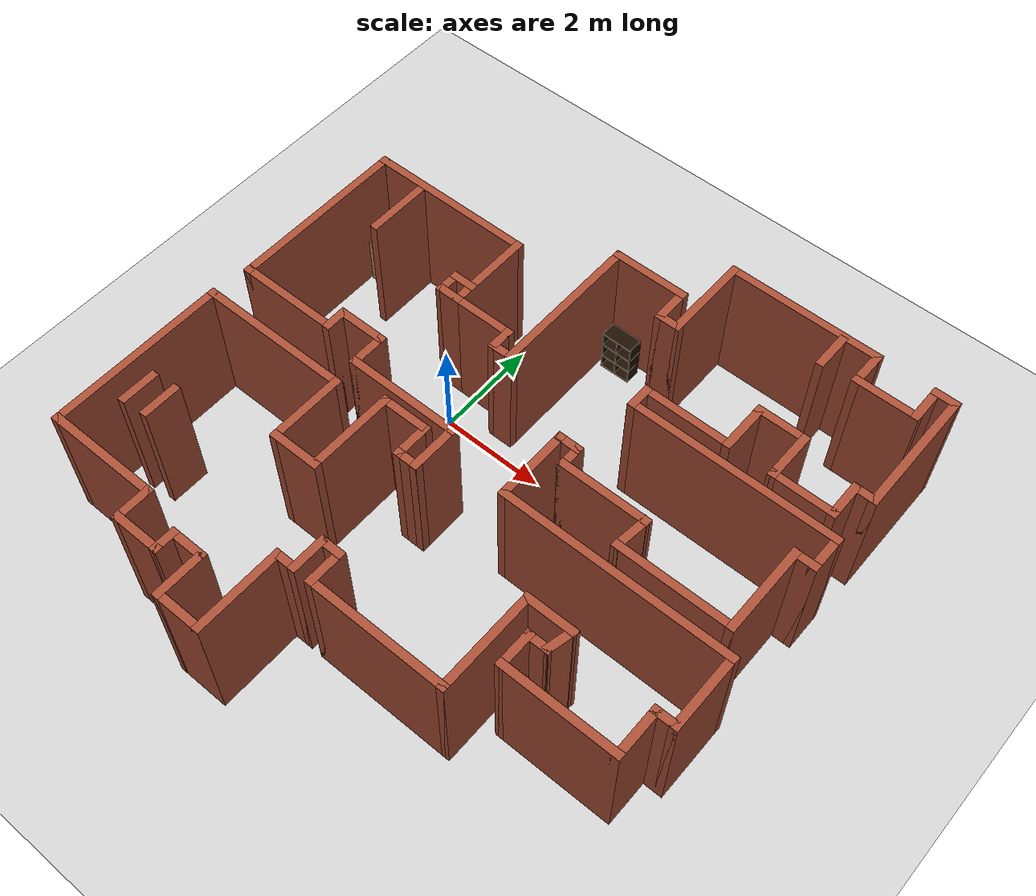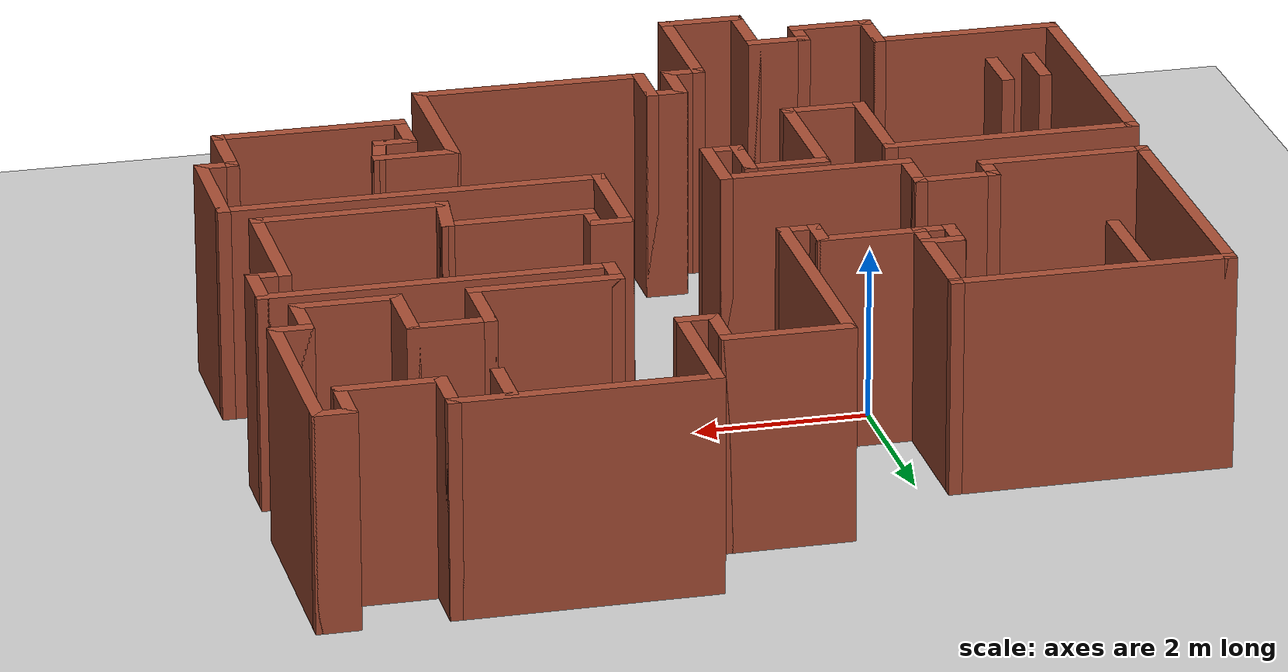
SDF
<sdf version="1.6">
 <world name="default">
  <light name="sun" type="directional">
   <pose>0 0 10 0 -0 0</pose>
   <diffuse>0.8 0.8 0.8 1</diffuse>
   <specular>0.2 0.2 0.2 1</specular>
   <attenuation>
    <range>1000</range>
    <constant>0.9</constant>
    <linear>0.01</linear>
    <quadratic>0.001</quadratic>
   </attenuation>
   <direction>-0.5 0.1 -0.9</direction>
  </light>
  <model name="ground_plane">
   <static>1</static>
   <link name="link">
    <collision name="collision">
     <geometry><plane><normal>0 0 1</normal><size>100 100</size></plane></geometry>
     <surface>
      <contact><collide_bitmask>65535</collide_bitmask></contact>
      <friction><ode><mu>100</mu><mu2>50</mu2></ode></friction>
     </surface>
    </collision>
    <visual name="visual">
     <cast_shadows>0</cast_shadows>
     <geometry><plane><normal>0 0 1</normal><size>100 100</size></plane></geometry>
     <material>
      <script><uri>file://media/materials/scripts/gazebo.material</uri><name>Gazebo/Grey</name></script>
     </material>
    </visual>
   </link>
  </model>
  <gravity>0 0 -9.8</gravity>
  <magnetic_field>6e-06 2.3e-05 -4.2e-05</magnetic_field>
  <atmosphere type="adiabatic"/>
  <physics name="default_physics" default="0" type="ode">
   <max_step_size>0.001</max_step_size>
   <real_time_factor>1</real_time_factor>
   <real_time_update_rate>1000</real_time_update_rate>
  </physics>
  <scene><ambient>0.4 0.4 0.4 1</ambient><background>0.7 0.7 0.7 1</background><shadows>1</shadows></scene>
  <audio><device>default</device></audio>
  <spherical_coordinates>
   <surface_model>EARTH_WGS84</surface_model>
   <latitude_deg>0</latitude_deg>
   <longitude_deg>0</longitude_deg>
   <elevation>0</elevation>
   <heading_deg>0</heading_deg>
  </spherical_coordinates>
  <model name="map_85">
   <pose>1.75927 -1.02662 0 0 -0 0</pose>
   <link name="Wall_0">
    <collision name="Wall_0_Collision">
     <geometry><box><size>3.25 0.15 2.5</size></box></geometry>
     <pose>0 0 1.25 0 -0 0</pose>
    </collision>
    <visual name="Wall_0_Visual">
     <pose>0 0 1.25 0 -0 0</pose>
     <geometry><box><size>3.25 0.15 2.5</size></box></geometry>
     <material>
      <script><uri>file://media/materials/scripts/gazebo.material</uri><name>Gazebo/Bricks</name></script>
      <ambient>1 1 1 1</ambient>
     </material>
     <meta><layer>0</layer></meta>
    </visual>
    <pose>-3.675 3.3 0 0 -0 3.14159</pose>
   </link>
   <link name="Wall_1">
    <collision name="Wall_1_Collision">
     <geometry><box><size>3.5 0.15 2.5</size></box></geometry>
     <pose>0 0 1.25 0 -0 0</pose>
    </collision>
    <visual name="Wall_1_Visual">
     <pose>0 0 1.25 0 -0 0</pose>
     <geometry><box><size>3.5 0.15 2.5</size></box></geometry>
     <material>
      <script><uri>file://media/materials/scripts/gazebo.material</uri><name>Gazebo/Bricks</name></script>
      <ambient>1 1 1 1</ambient>
     </material>
     <meta><layer>0</layer></meta>
    </visual>
    <pose>-5.225 1.625 0 0 -0 -1.5708</pose>
   </link>
   <link name="Wall_10">
    <collision name="Wall_10_Collision">
     <geometry><box><size>1 0.15 2.5</size></box></geometry>
     <pose>0 0 1.25 0 -0 0</pose>
    </collision>
    <visual name="Wall_10_Visual">
     <pose>0 0 1.25 0 -0 0</pose>
     <geometry><box><size>1 0.15 2.5</size></box></geometry>
     <material>
      <script><uri>file://media/materials/scripts/gazebo.material</uri><name>Gazebo/Bricks</name></script>
      <ambient>1 1 1 1</ambient>
     </material>
     <meta><layer>0</layer></meta>
    </visual>
    <pose>-1.2 -0.55 0 0 -0 3.14159</pose>
   </link>
   <link name="Wall_100">
    <collision name="Wall_100_Collision">
     <geometry><box><size>2.75 0.15 2.5</size></box></geometry>
     <pose>0 0 1.25 0 -0 0</pose>
    </collision>
    <visual name="Wall_100_Visual">
     <pose>0 0 1.25 0 -0 0</pose>
     <geometry><box><size>2.75 0.15 2.5</size></box></geometry>
     <material>
      <script><uri>file://media/materials/scripts/gazebo.material</uri><name>Gazebo/Bricks</name></script>
      <ambient>1 1 1 1</ambient>
     </material>
     <meta><layer>0</layer></meta>
    </visual>
    <pose>1.075 -3.65 0 0 -0 0</pose>
   </link>
   <link name="Wall_103">
    <collision name="Wall_103_Collision">
     <geometry><box><size>2 0.15 2.5</size></box></geometry>
     <pose>0 0 1.25 0 -0 0</pose>
    </collision>
    <visual name="Wall_103_Visual">
     <pose>0 0 1.25 0 -0 0</pose>
     <geometry><box><size>2 0.15 2.5</size></box></geometry>
     <material>
      <script><uri>file://media/materials/scripts/gazebo.material</uri><name>Gazebo/Bricks</name></script>
      <ambient>1 1 1 1</ambient>
     </material>
     <meta><layer>0</layer></meta>
    </visual>
    <pose>2.375 -2.725 0 0 -0 1.5708</pose>
   </link>
   <link name="Wall_105">
    <collision name="Wall_105_Collision">
     <geometry><box><size>1 0.15 2.5</size></box></geometry>
     <pose>0 0 1.25 0 -0 0</pose>
    </collision>
    <visual name="Wall_105_Visual">
     <pose>0 0 1.25 0 -0 0</pose>
     <geometry><box><size>1 0.15 2.5</size></box></geometry>
     <material>
      <script><uri>file://media/materials/scripts/gazebo.material</uri><name>Gazebo/Bricks</name></script>
      <ambient>1 1 1 1</ambient>
     </material>
     <meta><layer>0</layer></meta>
    </visual>
    <pose>2.8 -1.8 0 0 -0 0</pose>
   </link>
   <link name="Wall_106">
    <collision name="Wall_106_Collision">
     <geometry><box><size>0.610977 0.15 2.5</size></box></geometry>
     <pose>0 0 1.25 0 -0 0</pose>
    </collision>
    <visual name="Wall_106_Visual">
     <pose>0 0 1.25 0 -0 0</pose>
     <geometry><box><size>0.610977 0.15 2.5</size></box></geometry>
     <material>
      <script><uri>file://media/materials/scripts/gazebo.material</uri><name>Gazebo/Bricks</name></script>
      <ambient>1 1 1 1</ambient>
     </material>
     <meta><layer>0</layer></meta>
    </visual>
    <pose>3.175 -2.025 0 0 -0 -1.78947</pose>
   </link>
   <link name="Wall_108">
    <collision name="Wall_108_Collision">
     <geometry><box><size>0.75 0.15 2.5</size></box></geometry>
     <pose>0 0 1.25 0 -0 0</pose>
    </collision>
    <visual name="Wall_108_Visual">
     <pose>0 0 1.25 0 -0 0</pose>
     <geometry><box><size>0.75 0.15 2.5</size></box></geometry>
     <material>
      <script><uri>file://media/materials/scripts/gazebo.material</uri><name>Gazebo/Bricks</name></script>
      <ambient>1 1 1 1</ambient>
     </material>
     <meta><layer>0</layer></meta>
    </visual>
    <pose>3.2413 4.87358 0 0 -0 -1.5708</pose>
   </link>
   <link name="Wall_11">
    <collision name="Wall_11_Collision">
     <geometry><box><size>1.75 0.15 2.5</size></box></geometry>
     <pose>0 0 1.25 0 -0 0</pose>
    </collision>
    <visual name="Wall_11_Visual">
     <pose>0 0 1.25 0 -0 0</pose>
     <geometry><box><size>1.75 0.15 2.5</size></box></geometry>
     <material>
      <script><uri>file://media/materials/scripts/gazebo.material</uri><name>Gazebo/Bricks</name></script>
      <ambient>1 1 1 1</ambient>
     </material>
     <meta><layer>0</layer></meta>
    </visual>
    <pose>-1.625 -1.35 0 0 -0 -1.5708</pose>
   </link>
   <link name="Wall_110">
    <collision name="Wall_110_Collision">
     <geometry><box><size>0.75 0.15 2.5</size></box></geometry>
     <pose>0 0 1.25 0 -0 0</pose>
    </collision>
    <visual name="Wall_110_Visual">
     <pose>0 0 1.25 0 -0 0</pose>
     <geometry><box><size>0.75 0.15 2.5</size></box></geometry>
     <material>
      <script><uri>file://media/materials/scripts/gazebo.material</uri><name>Gazebo/Bricks</name></script>
      <ambient>1 1 1 1</ambient>
     </material>
     <meta><layer>0</layer></meta>
    </visual>
    <pose>-4.80815 -2.92144 0 0 -0 -1.5708</pose>
   </link>
   <link name="Wall_112">
    <collision name="Wall_112_Collision">
     <geometry><box><size>0.75 0.15 2.5</size></box></geometry>
     <pose>0 0 1.25 0 -0 0</pose>
    </collision>
    <visual name="Wall_112_Visual">
     <pose>0 0 1.25 0 -0 0</pose>
     <geometry><box><size>0.75 0.15 2.5</size></box></geometry>
     <material>
      <script><uri>file://media/materials/scripts/gazebo.material</uri><name>Gazebo/Bricks</name></script>
      <ambient>1 1 1 1</ambient>
     </material>
     <meta><layer>0</layer></meta>
    </visual>
    <pose>-4.34554 -2.87518 0 0 -0 -1.5708</pose>
   </link>
   <link name="Wall_12">
    <collision name="Wall_12_Collision">
     <geometry><box><size>1 0.15 2.5</size></box></geometry>
     <pose>0 0 1.25 0 -0 0</pose>
    </collision>
    <visual name="Wall_12_Visual">
     <pose>0 0 1.25 0 -0 0</pose>
     <geometry><box><size>1 0.15 2.5</size></box></geometry>
     <material>
      <script><uri>file://media/materials/scripts/gazebo.material</uri><name>Gazebo/Bricks</name></script>
      <ambient>1 1 1 1</ambient>
     </material>
     <meta><layer>0</layer></meta>
    </visual>
    <pose>-2.05 -2.15 0 0 -0 3.14159</pose>
   </link>
   <link name="Wall_13">
    <collision name="Wall_13_Collision">
     <geometry><box><size>1.5 0.15 2.5</size></box></geometry>
     <pose>0 0 1.25 0 -0 0</pose>
    </collision>
    <visual name="Wall_13_Visual">
     <pose>0 0 1.25 0 -0 0</pose>
     <geometry><box><size>1.5 0.15 2.5</size></box></geometry>
     <material>
      <script><uri>file://media/materials/scripts/gazebo.material</uri><name>Gazebo/Bricks</name></script>
      <ambient>1 1 1 1</ambient>
     </material>
     <meta><layer>0</layer></meta>
    </visual>
    <pose>-2.475 -1.475 0 0 -0 1.5708</pose>
   </link>
   <link name="Wall_14">
    <collision name="Wall_14_Collision">
     <geometry><box><size>3 0.15 2.5</size></box></geometry>
     <pose>0 0 1.25 0 -0 0</pose>
    </collision>
    <visual name="Wall_14_Visual">
     <pose>0 0 1.25 0 -0 0</pose>
     <geometry><box><size>3 0.15 2.5</size></box></geometry>
     <material>
      <script><uri>file://media/materials/scripts/gazebo.material</uri><name>Gazebo/Bricks</name></script>
      <ambient>1 1 1 1</ambient>
     </material>
     <meta><layer>0</layer></meta>
    </visual>
    <pose>-3.9 -0.8 0 0 -0 3.14159</pose>
   </link>
   <link name="Wall_15">
    <collision name="Wall_15_Collision">
     <geometry><box><size>3.5 0.15 2.5</size></box></geometry>
     <pose>0 0 1.25 0 -0 0</pose>
    </collision>
    <visual name="Wall_15_Visual">
     <pose>0 0 1.25 0 -0 0</pose>
     <geometry><box><size>3.5 0.15 2.5</size></box></geometry>
     <material>
      <script><uri>file://media/materials/scripts/gazebo.material</uri><name>Gazebo/Bricks</name></script>
      <ambient>1 1 1 1</ambient>
     </material>
     <meta><layer>0</layer></meta>
    </visual>
    <pose>-5.325 -2.475 0 0 -0 -1.5708</pose>
   </link>
   <link name="Wall_16">
    <collision name="Wall_16_Collision">
     <geometry><box><size>2.25 0.15 2.5</size></box></geometry>
     <pose>0 0 1.25 0 -0 0</pose>
    </collision>
    <visual name="Wall_16_Visual">
     <pose>0 0 1.25 0 -0 0</pose>
     <geometry><box><size>2.25 0.15 2.5</size></box></geometry>
     <material>
      <script><uri>file://media/materials/scripts/gazebo.material</uri><name>Gazebo/Bricks</name></script>
      <ambient>1 1 1 1</ambient>
     </material>
     <meta><layer>0</layer></meta>
    </visual>
    <pose>-4.275 -4.15 0 0 -0 0</pose>
   </link>
   <link name="Wall_17">
    <collision name="Wall_17_Collision">
     <geometry><box><size>0.75 0.15 2.5</size></box></geometry>
     <pose>0 0 1.25 0 -0 0</pose>
    </collision>
    <visual name="Wall_17_Visual">
     <pose>0 0 1.25 0 -0 0</pose>
     <geometry><box><size>0.75 0.15 2.5</size></box></geometry>
     <material>
      <script><uri>file://media/materials/scripts/gazebo.material</uri><name>Gazebo/Bricks</name></script>
      <ambient>1 1 1 1</ambient>
     </material>
     <meta><layer>0</layer></meta>
    </visual>
    <pose>-3.225 -4.45 0 0 -0 -1.5708</pose>
   </link>
   <link name="Wall_18">
    <collision name="Wall_18_Collision">
     <geometry><box><size>1 0.15 2.5</size></box></geometry>
     <pose>0 0 1.25 0 -0 0</pose>
    </collision>
    <visual name="Wall_18_Visual">
     <pose>0 0 1.25 0 -0 0</pose>
     <geometry><box><size>1 0.15 2.5</size></box></geometry>
     <material>
      <script><uri>file://media/materials/scripts/gazebo.material</uri><name>Gazebo/Bricks</name></script>
      <ambient>1 1 1 1</ambient>
     </material>
     <meta><layer>0</layer></meta>
    </visual>
    <pose>-2.8 -4.75 0 0 -0 0</pose>
   </link>
   <link name="Wall_19">
    <collision name="Wall_19_Collision">
     <geometry><box><size>0.5 0.15 2.5</size></box></geometry>
     <pose>0 0 1.25 0 -0 0</pose>
    </collision>
    <visual name="Wall_19_Visual">
     <pose>0 0 1.25 0 -0 0</pose>
     <geometry><box><size>0.5 0.15 2.5</size></box></geometry>
     <material>
      <script><uri>file://media/materials/scripts/gazebo.material</uri><name>Gazebo/Bricks</name></script>
      <ambient>1 1 1 1</ambient>
     </material>
     <meta><layer>0</layer></meta>
    </visual>
    <pose>-2.375 -4.575 0 0 -0 1.5708</pose>
   </link>
   <link name="Wall_2">
    <collision name="Wall_2_Collision">
     <geometry><box><size>2 0.15 2.5</size></box></geometry>
     <pose>0 0 1.25 0 -0 0</pose>
    </collision>
    <visual name="Wall_2_Visual">
     <pose>0 0 1.25 0 -0 0</pose>
     <geometry><box><size>2 0.15 2.5</size></box></geometry>
     <material>
      <script><uri>file://media/materials/scripts/gazebo.material</uri><name>Gazebo/Bricks</name></script>
      <ambient>1 1 1 1</ambient>
     </material>
     <meta><layer>0</layer></meta>
    </visual>
    <pose>-4.3 -0.05 0 0 -0 0</pose>
   </link>
   <link name="Wall_20">
    <collision name="Wall_20_Collision">
     <geometry><box><size>0.75 0.15 2.5</size></box></geometry>
     <pose>0 0 1.25 0 -0 0</pose>
    </collision>
    <visual name="Wall_20_Visual">
     <pose>0 0 1.25 0 -0 0</pose>
     <geometry><box><size>0.75 0.15 2.5</size></box></geometry>
     <material>
      <script><uri>file://media/materials/scripts/gazebo.material</uri><name>Gazebo/Bricks</name></script>
      <ambient>1 1 1 1</ambient>
     </material>
     <meta><layer>0</layer></meta>
    </visual>
    <pose>-2.075 -4.4 0 0 -0 0</pose>
   </link>
   <link name="Wall_21">
    <collision name="Wall_21_Collision">
     <geometry><box><size>1 0.15 2.5</size></box></geometry>
     <pose>0 0 1.25 0 -0 0</pose>
    </collision>
    <visual name="Wall_21_Visual">
     <pose>0 0 1.25 0 -0 0</pose>
     <geometry><box><size>1 0.15 2.5</size></box></geometry>
     <material>
      <script><uri>file://media/materials/scripts/gazebo.material</uri><name>Gazebo/Bricks</name></script>
      <ambient>1 1 1 1</ambient>
     </material>
     <meta><layer>0</layer></meta>
    </visual>
    <pose>-1.775 -4.825 0 0 -0 -1.5708</pose>
   </link>
   <link name="Wall_22">
    <collision name="Wall_22_Collision">
     <geometry><box><size>1 0.15 2.5</size></box></geometry>
     <pose>0 0 1.25 0 -0 0</pose>
    </collision>
    <visual name="Wall_22_Visual">
     <pose>0 0 1.25 0 -0 0</pose>
     <geometry><box><size>1 0.15 2.5</size></box></geometry>
     <material>
      <script><uri>file://media/materials/scripts/gazebo.material</uri><name>Gazebo/Bricks</name></script>
      <ambient>1 1 1 1</ambient>
     </material>
     <meta><layer>0</layer></meta>
    </visual>
    <pose>-1.35 -5.25 0 0 -0 0</pose>
   </link>
   <link name="Wall_3">
    <collision name="Wall_3_Collision">
     <geometry><box><size>0.5 0.15 2.5</size></box></geometry>
     <pose>0 0 1.25 0 -0 0</pose>
    </collision>
    <visual name="Wall_3_Visual">
     <pose>0 0 1.25 0 -0 0</pose>
     <geometry><box><size>0.5 0.15 2.5</size></box></geometry>
     <material>
      <script><uri>file://media/materials/scripts/gazebo.material</uri><name>Gazebo/Bricks</name></script>
      <ambient>1 1 1 1</ambient>
     </material>
     <meta><layer>0</layer></meta>
    </visual>
    <pose>-3.375 0.125 0 0 -0 1.5708</pose>
   </link>
   <link name="Wall_30">
    <collision name="Wall_30_Collision">
     <geometry><box><size>0.5 0.15 2.5</size></box></geometry>
     <pose>0 0 1.25 0 -0 0</pose>
    </collision>
    <visual name="Wall_30_Visual">
     <pose>0 0 1.25 0 -0 0</pose>
     <geometry><box><size>0.5 0.15 2.5</size></box></geometry>
     <material>
      <script><uri>file://media/materials/scripts/gazebo.material</uri><name>Gazebo/Bricks</name></script>
      <ambient>1 1 1 1</ambient>
     </material>
     <meta><layer>0</layer></meta>
    </visual>
    <pose>2.95 -2.25 0 0 -0 3.14159</pose>
   </link>
   <link name="Wall_31">
    <collision name="Wall_31_Collision">
     <geometry><box><size>0.75 0.15 2.5</size></box></geometry>
     <pose>0 0 1.25 0 -0 0</pose>
    </collision>
    <visual name="Wall_31_Visual">
     <pose>0 0 1.25 0 -0 0</pose>
     <geometry><box><size>0.75 0.15 2.5</size></box></geometry>
     <material>
      <script><uri>file://media/materials/scripts/gazebo.material</uri><name>Gazebo/Bricks</name></script>
      <ambient>1 1 1 1</ambient>
     </material>
     <meta><layer>0</layer></meta>
    </visual>
    <pose>2.775 -2.55 0 0 -0 -1.5708</pose>
   </link>
   <link name="Wall_32">
    <collision name="Wall_32_Collision">
     <geometry><box><size>2.25 0.15 2.5</size></box></geometry>
     <pose>0 0 1.25 0 -0 0</pose>
    </collision>
    <visual name="Wall_32_Visual">
     <pose>0 0 1.25 0 -0 0</pose>
     <geometry><box><size>2.25 0.15 2.5</size></box></geometry>
     <material>
      <script><uri>file://media/materials/scripts/gazebo.material</uri><name>Gazebo/Bricks</name></script>
      <ambient>1 1 1 1</ambient>
     </material>
     <meta><layer>0</layer></meta>
    </visual>
    <pose>3.825 -2.85 0 0 -0 0</pose>
   </link>
   <link name="Wall_33">
    <collision name="Wall_33_Collision">
     <geometry><box><size>1 0.15 2.5</size></box></geometry>
     <pose>0 0 1.25 0 -0 0</pose>
    </collision>
    <visual name="Wall_33_Visual">
     <pose>0 0 1.25 0 -0 0</pose>
     <geometry><box><size>1 0.15 2.5</size></box></geometry>
     <material>
      <script><uri>file://media/materials/scripts/gazebo.material</uri><name>Gazebo/Bricks</name></script>
      <ambient>1 1 1 1</ambient>
     </material>
     <meta><layer>0</layer></meta>
    </visual>
    <pose>4.875 -2.425 0 0 -0 1.5708</pose>
   </link>
   <link name="Wall_34">
    <collision name="Wall_34_Collision">
     <geometry><box><size>0.5 0.15 2.5</size></box></geometry>
     <pose>0 0 1.25 0 -0 0</pose>
    </collision>
    <visual name="Wall_34_Visual">
     <pose>0 0 1.25 0 -0 0</pose>
     <geometry><box><size>0.5 0.15 2.5</size></box></geometry>
     <material>
      <script><uri>file://media/materials/scripts/gazebo.material</uri><name>Gazebo/Bricks</name></script>
      <ambient>1 1 1 1</ambient>
     </material>
     <meta><layer>0</layer></meta>
    </visual>
    <pose>5.05 -2 0 0 -0 0</pose>
   </link>
   <link name="Wall_35">
    <collision name="Wall_35_Collision">
     <geometry><box><size>1.5 0.15 2.5</size></box></geometry>
     <pose>0 0 1.25 0 -0 0</pose>
    </collision>
    <visual name="Wall_35_Visual">
     <pose>0 0 1.25 0 -0 0</pose>
     <geometry><box><size>1.5 0.15 2.5</size></box></geometry>
     <material>
      <script><uri>file://media/materials/scripts/gazebo.material</uri><name>Gazebo/Bricks</name></script>
      <ambient>1 1 1 1</ambient>
     </material>
     <meta><layer>0</layer></meta>
    </visual>
    <pose>5.225 -1.325 0 0 -0 1.5708</pose>
   </link>
   <link name="Wall_38">
    <collision name="Wall_38_Collision">
     <geometry><box><size>4.43067 0.15 2.5</size></box></geometry>
     <pose>0 0 1.25 0 -0 0</pose>
    </collision>
    <visual name="Wall_38_Visual">
     <pose>0 0 1.25 0 -0 0</pose>
     <geometry><box><size>4.43067 0.15 2.5</size></box></geometry>
     <material>
      <script><uri>file://media/materials/scripts/gazebo.material</uri><name>Gazebo/Bricks</name></script>
      <ambient>1 1 1 1</ambient>
     </material>
     <meta><layer>0</layer></meta>
    </visual>
    <pose>3.0847 -0.65 0 0 -0 3.14159</pose>
   </link>
   <link name="Wall_4">
    <collision name="Wall_4_Collision">
     <geometry><box><size>1 0.15 2.5</size></box></geometry>
     <pose>0 0 1.25 0 -0 0</pose>
    </collision>
    <visual name="Wall_4_Visual">
     <pose>0 0 1.25 0 -0 0</pose>
     <geometry><box><size>1 0.15 2.5</size></box></geometry>
     <material>
      <script><uri>file://media/materials/scripts/gazebo.material</uri><name>Gazebo/Bricks</name></script>
      <ambient>1 1 1 1</ambient>
     </material>
     <meta><layer>0</layer></meta>
    </visual>
    <pose>-2.95 0.3 0 0 -0 0</pose>
   </link>
   <link name="Wall_44">
    <collision name="Wall_44_Collision">
     <geometry><box><size>2.25 0.15 2.5</size></box></geometry>
     <pose>0 0 1.25 0 -0 0</pose>
    </collision>
    <visual name="Wall_44_Visual">
     <pose>0 0 1.25 0 -0 0</pose>
     <geometry><box><size>2.25 0.15 2.5</size></box></geometry>
     <material>
      <script><uri>file://media/materials/scripts/gazebo.material</uri><name>Gazebo/Bricks</name></script>
      <ambient>1 1 1 1</ambient>
     </material>
     <meta><layer>0</layer></meta>
    </visual>
    <pose>3.875 -0.25 0 0 -0 0</pose>
   </link>
   <link name="Wall_45">
    <collision name="Wall_45_Collision">
     <geometry><box><size>1.75 0.15 2.5</size></box></geometry>
     <pose>0 0 1.25 0 -0 0</pose>
    </collision>
    <visual name="Wall_45_Visual">
     <pose>0 0 1.25 0 -0 0</pose>
     <geometry><box><size>1.75 0.15 2.5</size></box></geometry>
     <material>
      <script><uri>file://media/materials/scripts/gazebo.material</uri><name>Gazebo/Bricks</name></script>
      <ambient>1 1 1 1</ambient>
     </material>
     <meta><layer>0</layer></meta>
    </visual>
    <pose>4.925 0.55 0 0 -0 1.5708</pose>
   </link>
   <link name="Wall_46">
    <collision name="Wall_46_Collision">
     <geometry><box><size>0.5 0.15 2.5</size></box></geometry>
     <pose>0 0 1.25 0 -0 0</pose>
    </collision>
    <visual name="Wall_46_Visual">
     <pose>0 0 1.25 0 -0 0</pose>
     <geometry><box><size>0.5 0.15 2.5</size></box></geometry>
     <material>
      <script><uri>file://media/materials/scripts/gazebo.material</uri><name>Gazebo/Bricks</name></script>
      <ambient>1 1 1 1</ambient>
     </material>
     <meta><layer>0</layer></meta>
    </visual>
    <pose>5.1 1.35 0 0 -0 0</pose>
   </link>
   <link name="Wall_47">
    <collision name="Wall_47_Collision">
     <geometry><box><size>0.75 0.15 2.5</size></box></geometry>
     <pose>0 0 1.25 0 -0 0</pose>
    </collision>
    <visual name="Wall_47_Visual">
     <pose>0 0 1.25 0 -0 0</pose>
     <geometry><box><size>0.75 0.15 2.5</size></box></geometry>
     <material>
      <script><uri>file://media/materials/scripts/gazebo.material</uri><name>Gazebo/Bricks</name></script>
      <ambient>1 1 1 1</ambient>
     </material>
     <meta><layer>0</layer></meta>
    </visual>
    <pose>5.275 1.65 0 0 -0 1.5708</pose>
   </link>
   <link name="Wall_48">
    <collision name="Wall_48_Collision">
     <geometry><box><size>4 0.15 2.5</size></box></geometry>
     <pose>0 0 1.25 0 -0 0</pose>
    </collision>
    <visual name="Wall_48_Visual">
     <pose>0 0 1.25 0 -0 0</pose>
     <geometry><box><size>4 0.15 2.5</size></box></geometry>
     <material>
      <script><uri>file://media/materials/scripts/gazebo.material</uri><name>Gazebo/Bricks</name></script>
      <ambient>1 1 1 1</ambient>
     </material>
     <meta><layer>0</layer></meta>
    </visual>
    <pose>3.35 1.95 0 0 -0 3.14159</pose>
   </link>
   <link name="Wall_49">
    <collision name="Wall_49_Collision">
     <geometry><box><size>0.5 0.15 2.5</size></box></geometry>
     <pose>0 0 1.25 0 -0 0</pose>
    </collision>
    <visual name="Wall_49_Visual">
     <pose>0 0 1.25 0 -0 0</pose>
     <geometry><box><size>0.5 0.15 2.5</size></box></geometry>
     <material>
      <script><uri>file://media/materials/scripts/gazebo.material</uri><name>Gazebo/Bricks</name></script>
      <ambient>1 1 1 1</ambient>
     </material>
     <meta><layer>0</layer></meta>
    </visual>
    <pose>1.425 2.125 0 0 -0 1.5708</pose>
   </link>
   <link name="Wall_5">
    <collision name="Wall_5_Collision">
     <geometry><box><size>0.75 0.15 2.5</size></box></geometry>
     <pose>0 0 1.25 0 -0 0</pose>
    </collision>
    <visual name="Wall_5_Visual">
     <pose>0 0 1.25 0 -0 0</pose>
     <geometry><box><size>0.75 0.15 2.5</size></box></geometry>
     <material>
      <script><uri>file://media/materials/scripts/gazebo.material</uri><name>Gazebo/Bricks</name></script>
      <ambient>1 1 1 1</ambient>
     </material>
     <meta><layer>0</layer></meta>
    </visual>
    <pose>-2.525 -0 0 0 -0 -1.5708</pose>
   </link>
   <link name="Wall_50">
    <collision name="Wall_50_Collision">
     <geometry><box><size>1.75 0.15 2.5</size></box></geometry>
     <pose>0 0 1.25 0 -0 0</pose>
    </collision>
    <visual name="Wall_50_Visual">
     <pose>0 0 1.25 0 -0 0</pose>
     <geometry><box><size>1.75 0.15 2.5</size></box></geometry>
     <material>
      <script><uri>file://media/materials/scripts/gazebo.material</uri><name>Gazebo/Bricks</name></script>
      <ambient>1 1 1 1</ambient>
     </material>
     <meta><layer>0</layer></meta>
    </visual>
    <pose>2.225 2.3 0 0 -0 0</pose>
   </link>
   <link name="Wall_51">
    <collision name="Wall_51_Collision">
     <geometry><box><size>1 0.15 2.5</size></box></geometry>
     <pose>0 0 1.25 0 -0 0</pose>
    </collision>
    <visual name="Wall_51_Visual">
     <pose>0 0 1.25 0 -0 0</pose>
     <geometry><box><size>1 0.15 2.5</size></box></geometry>
     <material>
      <script><uri>file://media/materials/scripts/gazebo.material</uri><name>Gazebo/Bricks</name></script>
      <ambient>1 1 1 1</ambient>
     </material>
     <meta><layer>0</layer></meta>
    </visual>
    <pose>3.025 2.725 0 0 -0 1.5708</pose>
   </link>
   <link name="Wall_52">
    <collision name="Wall_52_Collision">
     <geometry><box><size>1 0.15 2.5</size></box></geometry>
     <pose>0 0 1.25 0 -0 0</pose>
    </collision>
    <visual name="Wall_52_Visual">
     <pose>0 0 1.25 0 -0 0</pose>
     <geometry><box><size>1 0.15 2.5</size></box></geometry>
     <material>
      <script><uri>file://media/materials/scripts/gazebo.material</uri><name>Gazebo/Bricks</name></script>
      <ambient>1 1 1 1</ambient>
     </material>
     <meta><layer>0</layer></meta>
    </visual>
    <pose>3.45 3.15 0 0 -0 0</pose>
   </link>
   <link name="Wall_53">
    <collision name="Wall_53_Collision">
     <geometry><box><size>1 0.15 2.5</size></box></geometry>
     <pose>0 0 1.25 0 -0 0</pose>
    </collision>
    <visual name="Wall_53_Visual">
     <pose>0 0 1.25 0 -0 0</pose>
     <geometry><box><size>1 0.15 2.5</size></box></geometry>
     <material>
      <script><uri>file://media/materials/scripts/gazebo.material</uri><name>Gazebo/Bricks</name></script>
      <ambient>1 1 1 1</ambient>
     </material>
     <meta><layer>0</layer></meta>
    </visual>
    <pose>3.875 2.725 0 0 -0 -1.5708</pose>
   </link>
   <link name="Wall_54">
    <collision name="Wall_54_Collision">
     <geometry><box><size>1.25 0.15 2.5</size></box></geometry>
     <pose>0 0 1.25 0 -0 0</pose>
    </collision>
    <visual name="Wall_54_Visual">
     <pose>0 0 1.25 0 -0 0</pose>
     <geometry><box><size>1.25 0.15 2.5</size></box></geometry>
     <material>
      <script><uri>file://media/materials/scripts/gazebo.material</uri><name>Gazebo/Bricks</name></script>
      <ambient>1 1 1 1</ambient>
     </material>
     <meta><layer>0</layer></meta>
    </visual>
    <pose>4.425 2.3 0 0 -0 0</pose>
   </link>
   <link name="Wall_55">
    <collision name="Wall_55_Collision">
     <geometry><box><size>0.75 0.15 2.5</size></box></geometry>
     <pose>0 0 1.25 0 -0 0</pose>
    </collision>
    <visual name="Wall_55_Visual">
     <pose>0 0 1.25 0 -0 0</pose>
     <geometry><box><size>0.75 0.15 2.5</size></box></geometry>
     <material>
      <script><uri>file://media/materials/scripts/gazebo.material</uri><name>Gazebo/Bricks</name></script>
      <ambient>1 1 1 1</ambient>
     </material>
     <meta><layer>0</layer></meta>
    </visual>
    <pose>4.975 2.6 0 0 -0 1.5708</pose>
   </link>
   <link name="Wall_56">
    <collision name="Wall_56_Collision">
     <geometry><box><size>0.5 0.15 2.5</size></box></geometry>
     <pose>0 0 1.25 0 -0 0</pose>
    </collision>
    <visual name="Wall_56_Visual">
     <pose>0 0 1.25 0 -0 0</pose>
     <geometry><box><size>0.5 0.15 2.5</size></box></geometry>
     <material>
      <script><uri>file://media/materials/scripts/gazebo.material</uri><name>Gazebo/Bricks</name></script>
      <ambient>1 1 1 1</ambient>
     </material>
     <meta><layer>0</layer></meta>
    </visual>
    <pose>5.15 2.9 0 0 -0 0</pose>
   </link>
   <link name="Wall_57">
    <collision name="Wall_57_Collision">
     <geometry><box><size>2.5 0.15 2.5</size></box></geometry>
     <pose>0 0 1.25 0 -0 0</pose>
    </collision>
    <visual name="Wall_57_Visual">
     <pose>0 0 1.25 0 -0 0</pose>
     <geometry><box><size>2.5 0.15 2.5</size></box></geometry>
     <material>
      <script><uri>file://media/materials/scripts/gazebo.material</uri><name>Gazebo/Bricks</name></script>
      <ambient>1 1 1 1</ambient>
     </material>
     <meta><layer>0</layer></meta>
    </visual>
    <pose>5.325 4.075 0 0 -0 1.5708</pose>
   </link>
   <link name="Wall_58">
    <collision name="Wall_58_Collision">
     <geometry><box><size>0.5 0.15 2.5</size></box></geometry>
     <pose>0 0 1.25 0 -0 0</pose>
    </collision>
    <visual name="Wall_58_Visual">
     <pose>0 0 1.25 0 -0 0</pose>
     <geometry><box><size>0.5 0.15 2.5</size></box></geometry>
     <material>
      <script><uri>file://media/materials/scripts/gazebo.material</uri><name>Gazebo/Bricks</name></script>
      <ambient>1 1 1 1</ambient>
     </material>
     <meta><layer>0</layer></meta>
    </visual>
    <pose>5.15 5.25 0 0 -0 3.14159</pose>
   </link>
   <link name="Wall_59">
    <collision name="Wall_59_Collision">
     <geometry><box><size>0.75 0.15 2.5</size></box></geometry>
     <pose>0 0 1.25 0 -0 0</pose>
    </collision>
    <visual name="Wall_59_Visual">
     <pose>0 0 1.25 0 -0 0</pose>
     <geometry><box><size>0.75 0.15 2.5</size></box></geometry>
     <material>
      <script><uri>file://media/materials/scripts/gazebo.material</uri><name>Gazebo/Bricks</name></script>
      <ambient>1 1 1 1</ambient>
     </material>
     <meta><layer>0</layer></meta>
    </visual>
    <pose>4.975 4.95 0 0 -0 -1.5708</pose>
   </link>
   <link name="Wall_6">
    <collision name="Wall_6_Collision">
     <geometry><box><size>2.25 0.15 2.5</size></box></geometry>
     <pose>0 0 1.25 0 -0 0</pose>
    </collision>
    <visual name="Wall_6_Visual">
     <pose>0 0 1.25 0 -0 0</pose>
     <geometry><box><size>2.25 0.15 2.5</size></box></geometry>
     <material>
      <script><uri>file://media/materials/scripts/gazebo.material</uri><name>Gazebo/Bricks</name></script>
      <ambient>1 1 1 1</ambient>
     </material>
     <meta><layer>0</layer></meta>
    </visual>
    <pose>-1.475 -0.3 0 0 -0 0</pose>
   </link>
   <link name="Wall_60">
    <collision name="Wall_60_Collision">
     <geometry><box><size>1.25 0.15 2.5</size></box></geometry>
     <pose>0 0 1.25 0 -0 0</pose>
    </collision>
    <visual name="Wall_60_Visual">
     <pose>0 0 1.25 0 -0 0</pose>
     <geometry><box><size>1.25 0.15 2.5</size></box></geometry>
     <material>
      <script><uri>file://media/materials/scripts/gazebo.material</uri><name>Gazebo/Bricks</name></script>
      <ambient>1 1 1 1</ambient>
     </material>
     <meta><layer>0</layer></meta>
    </visual>
    <pose>4.425 4.65 0 0 -0 3.14159</pose>
   </link>
   <link name="Wall_61">
    <collision name="Wall_61_Collision">
     <geometry><box><size>0.75 0.15 2.5</size></box></geometry>
     <pose>0 0 1.25 0 -0 0</pose>
    </collision>
    <visual name="Wall_61_Visual">
     <pose>0 0 1.25 0 -0 0</pose>
     <geometry><box><size>0.75 0.15 2.5</size></box></geometry>
     <material>
      <script><uri>file://media/materials/scripts/gazebo.material</uri><name>Gazebo/Bricks</name></script>
      <ambient>1 1 1 1</ambient>
     </material>
     <meta><layer>0</layer></meta>
    </visual>
    <pose>3.875 4.95 0 0 -0 1.5708</pose>
   </link>
   <link name="Wall_62">
    <collision name="Wall_62_Collision">
     <geometry><box><size>3 0.15 2.5</size></box></geometry>
     <pose>0 0 1.25 0 -0 0</pose>
    </collision>
    <visual name="Wall_62_Visual">
     <pose>0 0 1.25 0 -0 0</pose>
     <geometry><box><size>3 0.15 2.5</size></box></geometry>
     <material>
      <script><uri>file://media/materials/scripts/gazebo.material</uri><name>Gazebo/Bricks</name></script>
      <ambient>1 1 1 1</ambient>
     </material>
     <meta><layer>0</layer></meta>
    </visual>
    <pose>2.45 5.25 0 0 -0 3.14159</pose>
   </link>
   <link name="Wall_63">
    <collision name="Wall_63_Collision">
     <geometry><box><size>1.75 0.15 2.5</size></box></geometry>
     <pose>0 0 1.25 0 -0 0</pose>
    </collision>
    <visual name="Wall_63_Visual">
     <pose>0 0 1.25 0 -0 0</pose>
     <geometry><box><size>1.75 0.15 2.5</size></box></geometry>
     <material>
      <script><uri>file://media/materials/scripts/gazebo.material</uri><name>Gazebo/Bricks</name></script>
      <ambient>1 1 1 1</ambient>
     </material>
     <meta><layer>0</layer></meta>
    </visual>
    <pose>1.025 4.45 0 0 -0 -1.5708</pose>
   </link>
   <link name="Wall_64">
    <collision name="Wall_64_Collision">
     <geometry><box><size>0.5 0.15 2.5</size></box></geometry>
     <pose>0 0 1.25 0 -0 0</pose>
    </collision>
    <visual name="Wall_64_Visual">
     <pose>0 0 1.25 0 -0 0</pose>
     <geometry><box><size>0.5 0.15 2.5</size></box></geometry>
     <material>
      <script><uri>file://media/materials/scripts/gazebo.material</uri><name>Gazebo/Bricks</name></script>
      <ambient>1 1 1 1</ambient>
     </material>
     <meta><layer>0</layer></meta>
    </visual>
    <pose>0.85 3.65 0 0 -0 3.14159</pose>
   </link>
   <link name="Wall_65">
    <collision name="Wall_65_Collision">
     <geometry><box><size>0.75 0.15 2.5</size></box></geometry>
     <pose>0 0 1.25 0 -0 0</pose>
    </collision>
    <visual name="Wall_65_Visual">
     <pose>0 0 1.25 0 -0 0</pose>
     <geometry><box><size>0.75 0.15 2.5</size></box></geometry>
     <material>
      <script><uri>file://media/materials/scripts/gazebo.material</uri><name>Gazebo/Bricks</name></script>
      <ambient>1 1 1 1</ambient>
     </material>
     <meta><layer>0</layer></meta>
    </visual>
    <pose>0.675 3.95 0 0 -0 1.5708</pose>
   </link>
   <link name="Wall_68">
    <collision name="Wall_68_Collision">
     <geometry><box><size>1.5 0.15 2.5</size></box></geometry>
     <pose>0 0 1.25 0 -0 0</pose>
    </collision>
    <visual name="Wall_68_Visual">
     <pose>0 0 1.25 0 -0 0</pose>
     <geometry><box><size>1.5 0.15 2.5</size></box></geometry>
     <material>
      <script><uri>file://media/materials/scripts/gazebo.material</uri><name>Gazebo/Bricks</name></script>
      <ambient>1 1 1 1</ambient>
     </material>
     <meta><layer>0</layer></meta>
    </visual>
    <pose>0 4.25 0 0 -0 3.14159</pose>
   </link>
   <link name="Wall_69">
    <collision name="Wall_69_Collision">
     <geometry><box><size>3 0.15 2.5</size></box></geometry>
     <pose>0 0 1.25 0 -0 0</pose>
    </collision>
    <visual name="Wall_69_Visual">
     <pose>0 0 1.25 0 -0 0</pose>
     <geometry><box><size>3 0.15 2.5</size></box></geometry>
     <material>
      <script><uri>file://media/materials/scripts/gazebo.material</uri><name>Gazebo/Bricks</name></script>
      <ambient>1 1 1 1</ambient>
     </material>
     <meta><layer>0</layer></meta>
    </visual>
    <pose>-0.675 2.825 0 0 -0 -1.5708</pose>
   </link>
   <link name="Wall_7">
    <collision name="Wall_7_Collision">
     <geometry><box><size>1 0.15 2.5</size></box></geometry>
     <pose>0 0 1.25 0 -0 0</pose>
    </collision>
    <visual name="Wall_7_Visual">
     <pose>0 0 1.25 0 -0 0</pose>
     <geometry><box><size>1 0.15 2.5</size></box></geometry>
     <material>
      <script><uri>file://media/materials/scripts/gazebo.material</uri><name>Gazebo/Bricks</name></script>
      <ambient>1 1 1 1</ambient>
     </material>
     <meta><layer>0</layer></meta>
    </visual>
    <pose>-0.425 -0.725 0 0 -0 -1.5708</pose>
   </link>
   <link name="Wall_72">
    <collision name="Wall_72_Collision">
     <geometry><box><size>0.5 0.15 2.5</size></box></geometry>
     <pose>0 0 1.25 0 -0 0</pose>
    </collision>
    <visual name="Wall_72_Visual">
     <pose>0 0 1.25 0 -0 0</pose>
     <geometry><box><size>0.5 0.15 2.5</size></box></geometry>
     <material>
      <script><uri>file://media/materials/scripts/gazebo.material</uri><name>Gazebo/Bricks</name></script>
      <ambient>1 1 1 1</ambient>
     </material>
     <meta><layer>0</layer></meta>
    </visual>
    <pose>-0.85 1.4 0 0 -0 3.14159</pose>
   </link>
   <link name="Wall_73">
    <collision name="Wall_73_Collision">
     <geometry><box><size>0.5 0.15 2.5</size></box></geometry>
     <pose>0 0 1.25 0 -0 0</pose>
    </collision>
    <visual name="Wall_73_Visual">
     <pose>0 0 1.25 0 -0 0</pose>
     <geometry><box><size>0.5 0.15 2.5</size></box></geometry>
     <material>
      <script><uri>file://media/materials/scripts/gazebo.material</uri><name>Gazebo/Bricks</name></script>
      <ambient>1 1 1 1</ambient>
     </material>
     <meta><layer>0</layer></meta>
    </visual>
    <pose>-1.025 1.575 0 0 -0 1.5708</pose>
   </link>
   <link name="Wall_74">
    <collision name="Wall_74_Collision">
     <geometry><box><size>1.25 0.15 2.5</size></box></geometry>
     <pose>0 0 1.25 0 -0 0</pose>
    </collision>
    <visual name="Wall_74_Visual">
     <pose>0 0 1.25 0 -0 0</pose>
     <geometry><box><size>1.25 0.15 2.5</size></box></geometry>
     <material>
      <script><uri>file://media/materials/scripts/gazebo.material</uri><name>Gazebo/Bricks</name></script>
      <ambient>1 1 1 1</ambient>
     </material>
     <meta><layer>0</layer></meta>
    </visual>
    <pose>-1.575 1.75 0 0 -0 3.14159</pose>
   </link>
   <link name="Wall_75">
    <collision name="Wall_75_Collision">
     <geometry><box><size>1.7 0.15 2.5</size></box></geometry>
     <pose>0 0 1.25 0 -0 0</pose>
    </collision>
    <visual name="Wall_75_Visual">
     <pose>0 0 1.25 0 -0 0</pose>
     <geometry><box><size>1.7 0.15 2.5</size></box></geometry>
     <material>
      <script><uri>file://media/materials/scripts/gazebo.material</uri><name>Gazebo/Bricks</name></script>
      <ambient>1 1 1 1</ambient>
     </material>
     <meta><layer>0</layer></meta>
    </visual>
    <pose>-2.125 2.525 0 0 -0 1.5708</pose>
   </link>
   <link name="Wall_8">
    <collision name="Wall_8_Collision">
     <geometry><box><size>0.5 0.15 2.5</size></box></geometry>
     <pose>0 0 1.25 0 -0 0</pose>
    </collision>
    <visual name="Wall_8_Visual">
     <pose>0 0 1.25 0 -0 0</pose>
     <geometry><box><size>0.5 0.15 2.5</size></box></geometry>
     <material>
      <script><uri>file://media/materials/scripts/gazebo.material</uri><name>Gazebo/Bricks</name></script>
      <ambient>1 1 1 1</ambient>
     </material>
     <meta><layer>0</layer></meta>
    </visual>
    <pose>-0.6 -1.15 0 0 -0 3.14159</pose>
   </link>
   <link name="Wall_80">
    <collision name="Wall_80_Collision">
     <geometry><box><size>0.5 0.15 2.5</size></box></geometry>
     <pose>0 0 1.25 0 -0 0</pose>
    </collision>
    <visual name="Wall_80_Visual">
     <pose>0 0 1.25 0 -0 0</pose>
     <geometry><box><size>0.5 0.15 2.5</size></box></geometry>
     <material>
      <script><uri>file://media/materials/scripts/gazebo.material</uri><name>Gazebo/Bricks</name></script>
      <ambient>1 1 1 1</ambient>
     </material>
     <meta><layer>0</layer></meta>
    </visual>
    <pose>-2.3 1.75 0 0 -0 3.14159</pose>
   </link>
   <link name="Wall_81">
    <collision name="Wall_81_Collision">
     <geometry><box><size>0.5 0.15 2.5</size></box></geometry>
     <pose>0 0 1.25 0 -0 0</pose>
    </collision>
    <visual name="Wall_81_Visual">
     <pose>0 0 1.25 0 -0 0</pose>
     <geometry><box><size>0.5 0.15 2.5</size></box></geometry>
     <material>
      <script><uri>file://media/materials/scripts/gazebo.material</uri><name>Gazebo/Bricks</name></script>
      <ambient>1 1 1 1</ambient>
     </material>
     <meta><layer>0</layer></meta>
    </visual>
    <pose>-2.475 1.925 0 0 -0 1.5708</pose>
   </link>
   <link name="Wall_82">
    <collision name="Wall_82_Collision">
     <geometry><box><size>0.5 0.15 2.5</size></box></geometry>
     <pose>0 0 1.25 0 -0 0</pose>
    </collision>
    <visual name="Wall_82_Visual">
     <pose>0 0 1.25 0 -0 0</pose>
     <geometry><box><size>0.5 0.15 2.5</size></box></geometry>
     <material>
      <script><uri>file://media/materials/scripts/gazebo.material</uri><name>Gazebo/Bricks</name></script>
      <ambient>1 1 1 1</ambient>
     </material>
     <meta><layer>0</layer></meta>
    </visual>
    <pose>-2.3 2.1 0 0 -0 0</pose>
   </link>
   <link name="Wall_84">
    <collision name="Wall_84_Collision">
     <geometry><box><size>1.25 0.15 2.5</size></box></geometry>
     <pose>0 0 1.25 0 -0 0</pose>
    </collision>
    <visual name="Wall_84_Visual">
     <pose>0 0 1.25 0 -0 0</pose>
     <geometry><box><size>1.25 0.15 2.5</size></box></geometry>
     <material>
      <script><uri>file://media/materials/scripts/gazebo.material</uri><name>Gazebo/Bricks</name></script>
      <ambient>1 1 1 1</ambient>
     </material>
     <meta><layer>0</layer></meta>
    </visual>
    <pose>-4.27615 2.61122 0 0 -0 -1.5708</pose>
   </link>
   <link name="Wall_88">
    <collision name="Wall_88_Collision">
     <geometry><box><size>1.5 0.15 2.5</size></box></geometry>
     <pose>0 0 1.25 0 -0 0</pose>
    </collision>
    <visual name="Wall_88_Visual">
     <pose>0 0 1.25 0 -0 0</pose>
     <geometry><box><size>1.5 0.15 2.5</size></box></geometry>
     <material>
      <script><uri>file://media/materials/scripts/gazebo.material</uri><name>Gazebo/Bricks</name></script>
      <ambient>1 1 1 1</ambient>
     </material>
     <meta><layer>0</layer></meta>
    </visual>
    <pose>0.944392 0.025 0 0 -0 1.5708</pose>
   </link>
   <link name="Wall_89">
    <collision name="Wall_89_Collision">
     <geometry><box><size>0.5 0.15 2.5</size></box></geometry>
     <pose>0 0 1.25 0 -0 0</pose>
    </collision>
    <visual name="Wall_89_Visual">
     <pose>0 0 1.25 0 -0 0</pose>
     <geometry><box><size>0.5 0.15 2.5</size></box></geometry>
     <material>
      <script><uri>file://media/materials/scripts/gazebo.material</uri><name>Gazebo/Bricks</name></script>
      <ambient>1 1 1 1</ambient>
     </material>
     <meta><layer>0</layer></meta>
    </visual>
    <pose>1.11939 0.7 0 0 -0 0</pose>
   </link>
   <link name="Wall_9">
    <collision name="Wall_9_Collision">
     <geometry><box><size>0.75 0.15 2.5</size></box></geometry>
     <pose>0 0 1.25 0 -0 0</pose>
    </collision>
    <visual name="Wall_9_Visual">
     <pose>0 0 1.25 0 -0 0</pose>
     <geometry><box><size>0.75 0.15 2.5</size></box></geometry>
     <material>
      <script><uri>file://media/materials/scripts/gazebo.material</uri><name>Gazebo/Bricks</name></script>
      <ambient>1 1 1 1</ambient>
     </material>
     <meta><layer>0</layer></meta>
    </visual>
    <pose>-0.775 -0.85 0 0 -0 1.5708</pose>
   </link>
   <link name="Wall_90">
    <collision name="Wall_90_Collision">
     <geometry><box><size>0.5 0.15 2.5</size></box></geometry>
     <pose>0 0 1.25 0 -0 0</pose>
    </collision>
    <visual name="Wall_90_Visual">
     <pose>0 0 1.25 0 -0 0</pose>
     <geometry><box><size>0.5 0.15 2.5</size></box></geometry>
     <material>
      <script><uri>file://media/materials/scripts/gazebo.material</uri><name>Gazebo/Bricks</name></script>
      <ambient>1 1 1 1</ambient>
     </material>
     <meta><layer>0</layer></meta>
    </visual>
    <pose>1.29439 0.525 0 0 -0 -1.5708</pose>
   </link>
   <link name="Wall_92">
    <collision name="Wall_92_Collision">
     <geometry><box><size>1.75 0.15 2.5</size></box></geometry>
     <pose>0 0 1.25 0 -0 0</pose>
    </collision>
    <visual name="Wall_92_Visual">
     <pose>0 0 1.25 0 -0 0</pose>
     <geometry><box><size>1.75 0.15 2.5</size></box></geometry>
     <material>
      <script><uri>file://media/materials/scripts/gazebo.material</uri><name>Gazebo/Bricks</name></script>
      <ambient>1 1 1 1</ambient>
     </material>
     <meta><layer>0</layer></meta>
    </visual>
    <pose>2.09439 0.35 0 0 -0 0</pose>
   </link>
   <link name="Wall_93">
    <collision name="Wall_93_Collision">
     <geometry><box><size>0.753999 0.15 2.5</size></box></geometry>
     <pose>0 0 1.25 0 -0 0</pose>
    </collision>
    <visual name="Wall_93_Visual">
     <pose>0 0 1.25 0 -0 0</pose>
     <geometry><box><size>0.753999 0.15 2.5</size></box></geometry>
     <material>
      <script><uri>file://media/materials/scripts/gazebo.material</uri><name>Gazebo/Bricks</name></script>
      <ambient>1 1 1 1</ambient>
     </material>
     <meta><layer>0</layer></meta>
    </visual>
    <pose>2.8597 0.05 0 0 -0 -1.68594</pose>
   </link>
   <link name="Wall_95">
    <collision name="Wall_95_Collision">
     <geometry><box><size>1.75 0.15 2.5</size></box></geometry>
     <pose>0 0 1.25 0 -0 0</pose>
    </collision>
    <visual name="Wall_95_Visual">
     <pose>0 0 1.25 0 -0 0</pose>
     <geometry><box><size>1.75 0.15 2.5</size></box></geometry>
     <material>
      <script><uri>file://media/materials/scripts/gazebo.material</uri><name>Gazebo/Bricks</name></script>
      <ambient>1 1 1 1</ambient>
     </material>
     <meta><layer>0</layer></meta>
    </visual>
    <pose>-0.925 -4.45 0 0 -0 1.5708</pose>
   </link>
   <link name="Wall_96">
    <collision name="Wall_96_Collision">
     <geometry><box><size>0.5 0.15 2.5</size></box></geometry>
     <pose>0 0 1.25 0 -0 0</pose>
    </collision>
    <visual name="Wall_96_Visual">
     <pose>0 0 1.25 0 -0 0</pose>
     <geometry><box><size>0.5 0.15 2.5</size></box></geometry>
     <material>
      <script><uri>file://media/materials/scripts/gazebo.material</uri><name>Gazebo/Bricks</name></script>
      <ambient>1 1 1 1</ambient>
     </material>
     <meta><layer>0</layer></meta>
    </visual>
    <pose>-0.75 -3.65 0 0 -0 0</pose>
   </link>
   <link name="Wall_97">
    <collision name="Wall_97_Collision">
     <geometry><box><size>0.75 0.15 2.5</size></box></geometry>
     <pose>0 0 1.25 0 -0 0</pose>
    </collision>
    <visual name="Wall_97_Visual">
     <pose>0 0 1.25 0 -0 0</pose>
     <geometry><box><size>0.75 0.15 2.5</size></box></geometry>
     <material>
      <script><uri>file://media/materials/scripts/gazebo.material</uri><name>Gazebo/Bricks</name></script>
      <ambient>1 1 1 1</ambient>
     </material>
     <meta><layer>0</layer></meta>
    </visual>
    <pose>-0.575 -3.35 0 0 -0 1.5708</pose>
   </link>
   <link name="Wall_98">
    <collision name="Wall_98_Collision">
     <geometry><box><size>0.5 0.15 2.5</size></box></geometry>
     <pose>0 0 1.25 0 -0 0</pose>
    </collision>
    <visual name="Wall_98_Visual">
     <pose>0 0 1.25 0 -0 0</pose>
     <geometry><box><size>0.5 0.15 2.5</size></box></geometry>
     <material>
      <script><uri>file://media/materials/scripts/gazebo.material</uri><name>Gazebo/Bricks</name></script>
      <ambient>1 1 1 1</ambient>
     </material>
     <meta><layer>0</layer></meta>
    </visual>
    <pose>-0.4 -3.05 0 0 -0 0</pose>
   </link>
   <link name="Wall_99">
    <collision name="Wall_99_Collision">
     <geometry><box><size>0.75 0.15 2.5</size></box></geometry>
     <pose>0 0 1.25 0 -0 0</pose>
    </collision>
    <visual name="Wall_99_Visual">
     <pose>0 0 1.25 0 -0 0</pose>
     <geometry><box><size>0.75 0.15 2.5</size></box></geometry>
     <material>
      <script><uri>file://media/materials/scripts/gazebo.material</uri><name>Gazebo/Bricks</name></script>
      <ambient>1 1 1 1</ambient>
     </material>
     <meta><layer>0</layer></meta>
    </visual>
    <pose>-0.225 -3.35 0 0 -0 -1.5708</pose>
   </link>
   <static>1</static>
  </model>
  <model name="cabinet">
   <static>1</static>
   <link name="cabinet_bottom_plate">
    <inertial>
     <pose>0 0 -1 0 -0 0</pose>
     <inertia><ixx>2.05</ixx><ixy>0</ixy><ixz>0</ixz><iyy>2.05</iyy><iyz>0</iyz><izz>2.05</izz></inertia>
     <mass>25</mass>
    </inertial>
    <collision name="cabinet_bottom_plate_geom">
     <pose>0 0 0.01 0 -0 0</pose>
     <geometry><box><size>0.45 0.45 0.02</size></box></geometry>
    </collision>
    <visual name="cabinet_bottom_plate_geom_visual">
     <pose>0 0 0.01 0 -0 0</pose>
     <geometry><box><size>0.45 0.45 0.02</size></box></geometry>
     <material>
      <script><uri>file://media/materials/scripts/gazebo.material</uri><name>Gazebo/Wood</name></script>
     </material>
    </visual>
    <collision name="cabinet_bottom_plate_geom_cabinet_back_plate">
     <pose>0.235 0 0.51 0 -0 0</pose>
     <geometry><box><size>0.02 0.45 1.02</size></box></geometry>
    </collision>
    <visual name="cabinet_bottom_plate_geom_cabinet_back_plate_visual">
     <pose>0.235 0 0.51 0 -0 0</pose>
     <geometry><box><size>0.02 0.45 1.02</size></box></geometry>
     <material>
      <script><uri>file://media/materials/scripts/gazebo.material</uri><name>Gazebo/Wood</name></script>
     </material>
    </visual>
    <collision name="cabinet_bottom_plate_geom_cabinet_left_plate">
     <pose>0 0.235 0.51 0 -0 0</pose>
     <geometry><box><size>0.45 0.02 1.02</size></box></geometry>
    </collision>
    <visual name="cabinet_bottom_plate_geom_cabinet_left_plate_visual">
     <pose>0 0.235 0.51 0 -0 0</pose>
     <geometry><box><size>0.45 0.02 1.02</size></box></geometry>
     <material>
      <script><uri>file://media/materials/scripts/gazebo.material</uri><name>Gazebo/Wood</name></script>
     </material>
    </visual>
    <collision name="cabinet_bottom_plate_geom_cabinet_middle_plate">
     <pose>0 0 0.51 0 -0 0</pose>
     <geometry><box><size>0.45 0.45 0.02</size></box></geometry>
    </collision>
    <visual name="cabinet_bottom_plate_geom_cabinet_middle_plate_visual">
     <pose>0 0 0.51 0 -0 0</pose>
     <geometry><box><size>0.45 0.45 0.02</size></box></geometry>
     <material>
      <script><uri>file://media/materials/scripts/gazebo.material</uri><name>Gazebo/Wood</name></script>
     </material>
    </visual>
    <collision name="cabinet_bottom_plate_geom_cabinet_right_plate">
     <pose>0 -0.235 0.51 0 -0 0</pose>
     <geometry><box><size>0.45 0.02 1.02</size></box></geometry>
    </collision>
    <visual name="cabinet_bottom_plate_geom_cabinet_right_plate_visual">
     <pose>0 -0.235 0.51 0 -0 0</pose>
     <geometry><box><size>0.45 0.02 1.02</size></box></geometry>
     <material>
      <script><uri>file://media/materials/scripts/gazebo.material</uri><name>Gazebo/Wood</name></script>
     </material>
    </visual>
    <collision name="cabinet_bottom_plate_geom_cabinet_top_plate">
     <pose>0 0 1.01 0 -0 0</pose>
     <geometry><box><size>0.45 0.45 0.02</size></box></geometry>
    </collision>
    <visual name="cabinet_bottom_plate_geom_cabinet_top_plate_visual">
     <pose>0 0 1.01 0 -0 0</pose>
     <geometry><box><size>0.45 0.45 0.02</size></box></geometry>
     <material>
      <script><uri>file://media/materials/scripts/gazebo.material</uri><name>Gazebo/Wood</name></script>
     </material>
    </visual>
   </link>
   <pose>-1.1526 -5.46026 0 0 -0 0</pose>
  </model>
  <model name="6_Cube_StorageE">
   <link name="Wall_0">
    <pose>0 0 0.01 0 -0 0</pose>
    <inertial>
     <mass>1.6201</mass>
     <inertia><ixx>0.0119</ixx><iyy>0.0631</iyy><izz>0.0513</izz><ixy>0</ixy><ixz>0</ixz><iyz>0</iyz></inertia>
    </inertial>
    <collision name="Wall_0_Collision"><geometry><box><size>0.616 0.296 0.02</size></box></geometry></collision>
    <visual name="Wall_0_Visual">
     <geometry><box><size>0.616 0.296 0.02</size></box></geometry>
     <material>
      <script><uri>file://media/materials/scripts/gazebo.material</uri><name>Gazebo/Grey</name></script>
      <ambient>0.105882 0.0509804 0 1</ambient>
     </material>
    </visual>
   </link>
   <joint name="0_2" type="fixed">
    <pose>-0.308 0 0 0 -0 0</pose>
    <parent>Wall_2</parent>
    <child>Wall_0</child>
    <axis>
     <xyz>1 0 0</xyz>
     <use_parent_model_frame>0</use_parent_model_frame>
     <limit><lower>-1e+16</lower><upper>1e+16</upper></limit>
    </axis>
   </joint>
   <joint name="0_12" type="fixed">
    <parent>Wall_12</parent>
    <child>Wall_0</child>
    <axis>
     <xyz>0 0 1</xyz>
     <use_parent_model_frame>0</use_parent_model_frame>
     <limit><lower>-1e+16</lower><upper>1e+16</upper></limit>
    </axis>
   </joint>
   <joint name="0_4" type="fixed">
    <pose>0.308 0 0 0 -0 0</pose>
    <parent>Wall_4</parent>
    <child>Wall_0</child>
    <axis>
     <xyz>1 0 0</xyz>
     <use_parent_model_frame>0</use_parent_model_frame>
     <limit><lower>-1e+16</lower><upper>1e+16</upper></limit>
    </axis>
   </joint>
   <link name="Wall_10">
    <pose>0 0 0.61 0 -0 0</pose>
    <inertial>
     <mass>1.6201</mass>
     <inertia><ixx>0.0119</ixx><iyy>0.0631</iyy><izz>0.0513</izz><ixy>0</ixy><ixz>0</ixz><iyz>0</iyz></inertia>
    </inertial>
    <collision name="Wall_10_Collision"><geometry><box><size>0.616 0.296 0.02</size></box></geometry></collision>
    <visual name="Wall_10_Visual">
     <geometry><box><size>0.616 0.296 0.02</size></box></geometry>
     <material>
      <script><uri>file://media/materials/scripts/gazebo.material</uri><name>Gazebo/Grey</name></script>
      <ambient>0.105882 0.0509804 0 1</ambient>
     </material>
    </visual>
   </link>
   <joint name="10_2" type="fixed">
    <pose>-0.308 0 0 0 -0 0</pose>
    <parent>Wall_2</parent>
    <child>Wall_10</child>
    <axis>
     <xyz>1 0 0</xyz>
     <use_parent_model_frame>0</use_parent_model_frame>
     <limit><lower>-1e+16</lower><upper>1e+16</upper></limit>
    </axis>
   </joint>
   <joint name="10_12" type="fixed">
    <parent>Wall_12</parent>
    <child>Wall_10</child>
    <axis>
     <xyz>0 0 1</xyz>
     <use_parent_model_frame>0</use_parent_model_frame>
     <limit><lower>-1e+16</lower><upper>1e+16</upper></limit>
    </axis>
   </joint>
   <joint name="10_4" type="fixed">
    <pose>0.308 0 0 0 -0 0</pose>
    <parent>Wall_4</parent>
    <child>Wall_10</child>
    <axis>
     <xyz>1 0 0</xyz>
     <use_parent_model_frame>0</use_parent_model_frame>
     <limit><lower>-1e+16</lower><upper>1e+16</upper></limit>
    </axis>
   </joint>
   <link name="Wall_12">
    <pose>0 0 0.4575 0 -0 0</pose>
    <inertial>
     <mass>2.4065</mass>
     <inertia><ixx>0.0177</ixx><iyy>0.1855</iyy><izz>0.168</izz><ixy>0</ixy><ixz>0</ixz><iyz>0</iyz></inertia>
    </inertial>
    <collision name="Wall_12_Collision"><geometry><box><size>0.02 0.296 0.915</size></box></geometry></collision>
    <visual name="Wall_12_Visual">
     <geometry><box><size>0.02 0.296 0.915</size></box></geometry>
     <material>
      <script><uri>file://media/materials/scripts/gazebo.material</uri><name>Gazebo/Grey</name></script>
      <ambient>0.105882 0.0509804 0 1</ambient>
     </material>
    </visual>
   </link>
   <link name="Wall_2">
    <pose>-0.298 0 0.4575 0 -0 0</pose>
    <inertial>
     <mass>2.4065</mass>
     <inertia><ixx>0.0177</ixx><iyy>0.1855</iyy><izz>0.168</izz><ixy>0</ixy><ixz>0</ixz><iyz>0</iyz></inertia>
    </inertial>
    <collision name="Wall_2_Collision"><geometry><box><size>0.02 0.296 0.915</size></box></geometry></collision>
    <visual name="Wall_2_Visual">
     <geometry><box><size>0.02 0.296 0.915</size></box></geometry>
     <material>
      <script><uri>file://media/materials/scripts/gazebo.material</uri><name>Gazebo/Grey</name></script>
      <ambient>0.105882 0.0509804 0 1</ambient>
     </material>
    </visual>
   </link>
   <link name="Wall_4">
    <pose>0.298 0 0.4575 0 -0 0</pose>
    <inertial>
     <mass>2.4065</mass>
     <inertia><ixx>0.0177</ixx><iyy>0.1855</iyy><izz>0.168</izz><ixy>0</ixy><ixz>0</ixz><iyz>0</iyz></inertia>
    </inertial>
    <collision name="Wall_4_Collision"><geometry><box><size>0.02 0.296 0.915</size></box></geometry></collision>
    <visual name="Wall_4_Visual">
     <geometry><box><size>0.02 0.296 0.915</size></box></geometry>
     <material>
      <script><uri>file://media/materials/scripts/gazebo.material</uri><name>Gazebo/Grey</name></script>
      <ambient>0.105882 0.0509804 0 1</ambient>
     </material>
    </visual>
   </link>
   <link name="Wall_6">
    <pose>0 0 0.905 0 -0 0</pose>
    <inertial>
     <mass>1.6201</mass>
     <inertia><ixx>0.0119</ixx><iyy>0.0631</iyy><izz>0.0513</izz><ixy>0</ixy><ixz>0</ixz><iyz>0</iyz></inertia>
    </inertial>
    <collision name="Wall_6_Collision"><geometry><box><size>0.616 0.296 0.02</size></box></geometry></collision>
    <visual name="Wall_6_Visual">
     <geometry><box><size>0.616 0.296 0.02</size></box></geometry>
     <material>
      <script><uri>file://media/materials/scripts/gazebo.material</uri><name>Gazebo/Grey</name></script>
      <ambient>0.105882 0.0509804 0 1</ambient>
     </material>
    </visual>
   </link>
   <joint name="6_2" type="fixed">
    <pose>-0.308 0 0 0 -0 0</pose>
    <parent>Wall_2</parent>
    <child>Wall_6</child>
    <axis>
     <xyz>2 0 0</xyz>
     <use_parent_model_frame>0</use_parent_model_frame>
     <limit><lower>-1e+16</lower><upper>1e+16</upper></limit>
    </axis>
   </joint>
   <joint name="6_12" type="fixed">
    <parent>Wall_12</parent>
    <child>Wall_6</child>
    <axis>
     <xyz>0 0 1</xyz>
     <use_parent_model_frame>0</use_parent_model_frame>
     <limit><lower>-1e+16</lower><upper>1e+16</upper></limit>
    </axis>
   </joint>
   <joint name="6_4" type="fixed">
    <pose>0.308 0 0 0 -0 0</pose>
    <parent>Wall_4</parent>
    <child>Wall_6</child>
    <axis>
     <xyz>1 0 0</xyz>
     <use_parent_model_frame>0</use_parent_model_frame>
     <limit><lower>-1e+16</lower><upper>1e+16</upper></limit>
    </axis>
   </joint>
   <link name="Wall_8">
    <pose>0 0 0.305 0 -0 0</pose>
    <inertial>
     <mass>1.6201</mass>
     <inertia><ixx>0.0119</ixx><iyy>0.0631</iyy><izz>0.0513</izz><ixy>0</ixy><ixz>0</ixz><iyz>0</iyz></inertia>
    </inertial>
    <collision name="Wall_8_Collision"><geometry><box><size>0.616 0.296 0.02</size></box></geometry></collision>
    <visual name="Wall_8_Visual">
     <geometry><box><size>0.616 0.296 0.02</size></box></geometry>
     <material>
      <script><uri>file://media/materials/scripts/gazebo.material</uri><name>Gazebo/Grey</name></script>
      <ambient>0.105882 0.0509804 0 1</ambient>
     </material>
    </visual>
   </link>
   <joint name="8_2" type="fixed">
    <pose>-0.308 0 0 0 -0 0</pose>
    <parent>Wall_2</parent>
    <child>Wall_8</child>
    <axis>
     <xyz>1 0 0</xyz>
     <use_parent_model_frame>0</use_parent_model_frame>
     <limit><lower>-1e+16</lower><upper>1e+16</upper></limit>
    </axis>
   </joint>
   <joint name="8_12" type="fixed">
    <parent>Wall_12</parent>
    <child>Wall_8</child>
    <axis>
     <xyz>0 0 1</xyz>
     <use_parent_model_frame>0</use_parent_model_frame>
     <limit><lower>-1e+16</lower><upper>1e+16</upper></limit>
    </axis>
   </joint>
   <joint name="8_4" type="fixed">
    <pose>0.308 0 0 0 -0 0</pose>
    <parent>Wall_4</parent>
    <child>Wall_8</child>
    <axis>
     <xyz>1 0 0</xyz>
     <use_parent_model_frame>0</use_parent_model_frame>
     <limit><lower>-1e+16</lower><upper>1e+16</upper></limit>
    </axis>
   </joint>
   <static>1</static>
   <pose>-2.86431 -0.845877 0 0 -0 0</pose>
  </model>
  <model name="6_Cube_StorageE_0">
   <link name="Wall_0">
    <pose>0 0 0.01 0 -0 0</pose>
    <inertial>
     <mass>1.6201</mass>
     <inertia><ixx>0.0119</ixx><iyy>0.0631</iyy><izz>0.0513</izz><ixy>0</ixy><ixz>0</ixz><iyz>0</iyz></inertia>
    </inertial>
    <collision name="Wall_0_Collision"><geometry><box><size>0.616 0.296 0.02</size></box></geometry></collision>
    <visual name="Wall_0_Visual">
     <geometry><box><size>0.616 0.296 0.02</size></box></geometry>
     <material>
      <script><uri>file://media/materials/scripts/gazebo.material</uri><name>Gazebo/Grey</name></script>
      <ambient>0.105882 0.0509804 0 1</ambient>
     </material>
    </visual>
   </link>
   <joint name="0_2" type="fixed">
    <pose>-0.308 0 0 0 -0 0</pose>
    <parent>Wall_2</parent>
    <child>Wall_0</child>
    <axis>
     <xyz>1 0 0</xyz>
     <use_parent_model_frame>0</use_parent_model_frame>
     <limit><lower>-1e+16</lower><upper>1e+16</upper></limit>
    </axis>
   </joint>
   <joint name="0_12" type="fixed">
    <parent>Wall_12</parent>
    <child>Wall_0</child>
    <axis>
     <xyz>0 0 1</xyz>
     <use_parent_model_frame>0</use_parent_model_frame>
     <limit><lower>-1e+16</lower><upper>1e+16</upper></limit>
    </axis>
   </joint>
   <joint name="0_4" type="fixed">
    <pose>0.308 0 0 0 -0 0</pose>
    <parent>Wall_4</parent>
    <child>Wall_0</child>
    <axis>
     <xyz>1 0 0</xyz>
     <use_parent_model_frame>0</use_parent_model_frame>
     <limit><lower>-1e+16</lower><upper>1e+16</upper></limit>
    </axis>
   </joint>
   <link name="Wall_10">
    <pose>0 0 0.61 0 -0 0</pose>
    <inertial>
     <mass>1.6201</mass>
     <inertia><ixx>0.0119</ixx><iyy>0.0631</iyy><izz>0.0513</izz><ixy>0</ixy><ixz>0</ixz><iyz>0</iyz></inertia>
    </inertial>
    <collision name="Wall_10_Collision"><geometry><box><size>0.616 0.296 0.02</size></box></geometry></collision>
    <visual name="Wall_10_Visual">
     <geometry><box><size>0.616 0.296 0.02</size></box></geometry>
     <material>
      <script><uri>file://media/materials/scripts/gazebo.material</uri><name>Gazebo/Grey</name></script>
      <ambient>0.105882 0.0509804 0 1</ambient>
     </material>
    </visual>
   </link>
   <joint name="10_2" type="fixed">
    <pose>-0.308 0 0 0 -0 0</pose>
    <parent>Wall_2</parent>
    <child>Wall_10</child>
    <axis>
     <xyz>1 0 0</xyz>
     <use_parent_model_frame>0</use_parent_model_frame>
     <limit><lower>-1e+16</lower><upper>1e+16</upper></limit>
    </axis>
   </joint>
   <joint name="10_12" type="fixed">
    <parent>Wall_12</parent>
    <child>Wall_10</child>
    <axis>
     <xyz>0 0 1</xyz>
     <use_parent_model_frame>0</use_parent_model_frame>
     <limit><lower>-1e+16</lower><upper>1e+16</upper></limit>
    </axis>
   </joint>
   <joint name="10_4" type="fixed">
    <pose>0.308 0 0 0 -0 0</pose>
    <parent>Wall_4</parent>
    <child>Wall_10</child>
    <axis>
     <xyz>1 0 0</xyz>
     <use_parent_model_frame>0</use_parent_model_frame>
     <limit><lower>-1e+16</lower><upper>1e+16</upper></limit>
    </axis>
   </joint>
   <link name="Wall_12">
    <pose>0 0 0.4575 0 -0 0</pose>
    <inertial>
     <mass>2.4065</mass>
     <inertia><ixx>0.0177</ixx><iyy>0.1855</iyy><izz>0.168</izz><ixy>0</ixy><ixz>0</ixz><iyz>0</iyz></inertia>
    </inertial>
    <collision name="Wall_12_Collision"><geometry><box><size>0.02 0.296 0.915</size></box></geometry></collision>
    <visual name="Wall_12_Visual">
     <geometry><box><size>0.02 0.296 0.915</size></box></geometry>
     <material>
      <script><uri>file://media/materials/scripts/gazebo.material</uri><name>Gazebo/Grey</name></script>
      <ambient>0.105882 0.0509804 0 1</ambient>
     </material>
    </visual>
   </link>
   <link name="Wall_2">
    <pose>-0.298 0 0.4575 0 -0 0</pose>
    <inertial>
     <mass>2.4065</mass>
     <inertia><ixx>0.0177</ixx><iyy>0.1855</iyy><izz>0.168</izz><ixy>0</ixy><ixz>0</ixz><iyz>0</iyz></inertia>
    </inertial>
    <collision name="Wall_2_Collision"><geometry><box><size>0.02 0.296 0.915</size></box></geometry></collision>
    <visual name="Wall_2_Visual">
     <geometry><box><size>0.02 0.296 0.915</size></box></geometry>
     <material>
      <script><uri>file://media/materials/scripts/gazebo.material</uri><name>Gazebo/Grey</name></script>
      <ambient>0.105882 0.0509804 0 1</ambient>
     </material>
    </visual>
   </link>
   <link name="Wall_4">
    <pose>0.298 0 0.4575 0 -0 0</pose>
    <inertial>
     <mass>2.4065</mass>
     <inertia><ixx>0.0177</ixx><iyy>0.1855</iyy><izz>0.168</izz><ixy>0</ixy><ixz>0</ixz><iyz>0</iyz></inertia>
    </inertial>
    <collision name="Wall_4_Collision"><geometry><box><size>0.02 0.296 0.915</size></box></geometry></collision>
    <visual name="Wall_4_Visual">
     <geometry><box><size>0.02 0.296 0.915</size></box></geometry>
     <material>
      <script><uri>file://media/materials/scripts/gazebo.material</uri><name>Gazebo/Grey</name></script>
      <ambient>0.105882 0.0509804 0 1</ambient>
     </material>
    </visual>
   </link>
   <link name="Wall_6">
    <pose>0 0 0.905 0 -0 0</pose>
    <inertial>
     <mass>1.6201</mass>
     <inertia><ixx>0.0119</ixx><iyy>0.0631</iyy><izz>0.0513</izz><ixy>0</ixy><ixz>0</ixz><iyz>0</iyz></inertia>
    </inertial>
    <collision name="Wall_6_Collision"><geometry><box><size>0.616 0.296 0.02</size></box></geometry></collision>
    <visual name="Wall_6_Visual">
     <geometry><box><size>0.616 0.296 0.02</size></box></geometry>
     <material>
      <script><uri>file://media/materials/scripts/gazebo.material</uri><name>Gazebo/Grey</name></script>
      <ambient>0.105882 0.0509804 0 1</ambient>
     </material>
    </visual>
   </link>
   <joint name="6_2" type="fixed">
    <pose>-0.308 0 0 0 -0 0</pose>
    <parent>Wall_2</parent>
    <child>Wall_6</child>
    <axis>
     <xyz>2 0 0</xyz>
     <use_parent_model_frame>0</use_parent_model_frame>
     <limit><lower>-1e+16</lower><upper>1e+16</upper></limit>
    </axis>
   </joint>
   <joint name="6_12" type="fixed">
    <parent>Wall_12</parent>
    <child>Wall_6</child>
    <axis>
     <xyz>0 0 1</xyz>
     <use_parent_model_frame>0</use_parent_model_frame>
     <limit><lower>-1e+16</lower><upper>1e+16</upper></limit>
    </axis>
   </joint>
   <joint name="6_4" type="fixed">
    <pose>0.308 0 0 0 -0 0</pose>
    <parent>Wall_4</parent>
    <child>Wall_6</child>
    <axis>
     <xyz>1 0 0</xyz>
     <use_parent_model_frame>0</use_parent_model_frame>
     <limit><lower>-1e+16</lower><upper>1e+16</upper></limit>
    </axis>
   </joint>
   <link name="Wall_8">
    <pose>0 0 0.305 0 -0 0</pose>
    <inertial>
     <mass>1.6201</mass>
     <inertia><ixx>0.0119</ixx><iyy>0.0631</iyy><izz>0.0513</izz><ixy>0</ixy><ixz>0</ixz><iyz>0</iyz></inertia>
    </inertial>
    <collision name="Wall_8_Collision"><geometry><box><size>0.616 0.296 0.02</size></box></geometry></collision>
    <visual name="Wall_8_Visual">
     <geometry><box><size>0.616 0.296 0.02</size></box></geometry>
     <material>
      <script><uri>file://media/materials/scripts/gazebo.material</uri><name>Gazebo/Grey</name></script>
      <ambient>0.105882 0.0509804 0 1</ambient>
     </material>
    </visual>
   </link>
   <joint name="8_2" type="fixed">
    <pose>-0.308 0 0 0 -0 0</pose>
    <parent>Wall_2</parent>
    <child>Wall_8</child>
    <axis>
     <xyz>1 0 0</xyz>
     <use_parent_model_frame>0</use_parent_model_frame>
     <limit><lower>-1e+16</lower><upper>1e+16</upper></limit>
    </axis>
   </joint>
   <joint name="8_12" type="fixed">
    <parent>Wall_12</parent>
    <child>Wall_8</child>
    <axis>
     <xyz>0 0 1</xyz>
     <use_parent_model_frame>0</use_parent_model_frame>
     <limit><lower>-1e+16</lower><upper>1e+16</upper></limit>
    </axis>
   </joint>
   <joint name="8_4" type="fixed">
    <pose>0.308 0 0 0 -0 0</pose>
    <parent>Wall_4</parent>
    <child>Wall_8</child>
    <axis>
     <xyz>1 0 0</xyz>
     <use_parent_model_frame>0</use_parent_model_frame>
     <limit><lower>-1e+16</lower><upper>1e+16</upper></limit>
    </axis>
   </joint>
   <static>1</static>
   <pose>1.54365 2.89744 0 0 -0 0</pose>
  </model>
  <model name="cabinet_0">
   <static>1</static>
   <link name="cabinet_bottom_plate">
    <inertial>
     <pose>0 0 -1 0 -0 0</pose>
     <inertia><ixx>2.05</ixx><ixy>0</ixy><ixz>0</ixz><iyy>2.05</iyy><iyz>0</iyz><izz>2.05</izz></inertia>
     <mass>25</mass>
    </inertial>
    <collision name="cabinet_bottom_plate_geom">
     <pose>0 0 0.01 0 -0 0</pose>
     <geometry><box><size>0.45 0.45 0.02</size></box></geometry>
    </collision>
    <visual name="cabinet_bottom_plate_geom_visual">
     <pose>0 0 0.01 0 -0 0</pose>
     <geometry><box><size>0.45 0.45 0.02</size></box></geometry>
     <material>
      <script><uri>file://media/materials/scripts/gazebo.material</uri><name>Gazebo/Wood</name></script>
     </material>
    </visual>
    <collision name="cabinet_bottom_plate_geom_cabinet_back_plate">
     <pose>0.235 0 0.51 0 -0 0</pose>
     <geometry><box><size>0.02 0.45 1.02</size></box></geometry>
    </collision>
    <visual name="cabinet_bottom_plate_geom_cabinet_back_plate_visual">
     <pose>0.235 0 0.51 0 -0 0</pose>
     <geometry><box><size>0.02 0.45 1.02</size></box></geometry>
     <material>
      <script><uri>file://media/materials/scripts/gazebo.material</uri><name>Gazebo/Wood</name></script>
     </material>
    </visual>
    <collision name="cabinet_bottom_plate_geom_cabinet_left_plate">
     <pose>0 0.235 0.51 0 -0 0</pose>
     <geometry><box><size>0.45 0.02 1.02</size></box></geometry>
    </collision>
    <visual name="cabinet_bottom_plate_geom_cabinet_left_plate_visual">
     <pose>0 0.235 0.51 0 -0 0</pose>
     <geometry><box><size>0.45 0.02 1.02</size></box></geometry>
     <material>
      <script><uri>file://media/materials/scripts/gazebo.material</uri><name>Gazebo/Wood</name></script>
     </material>
    </visual>
    <collision name="cabinet_bottom_plate_geom_cabinet_middle_plate">
     <pose>0 0 0.51 0 -0 0</pose>
     <geometry><box><size>0.45 0.45 0.02</size></box></geometry>
    </collision>
    <visual name="cabinet_bottom_plate_geom_cabinet_middle_plate_visual">
     <pose>0 0 0.51 0 -0 0</pose>
     <geometry><box><size>0.45 0.45 0.02</size></box></geometry>
     <material>
      <script><uri>file://media/materials/scripts/gazebo.material</uri><name>Gazebo/Wood</name></script>
     </material>
    </visual>
    <collision name="cabinet_bottom_plate_geom_cabinet_right_plate">
     <pose>0 -0.235 0.51 0 -0 0</pose>
     <geometry><box><size>0.45 0.02 1.02</size></box></geometry>
    </collision>
    <visual name="cabinet_bottom_plate_geom_cabinet_right_plate_visual">
     <pose>0 -0.235 0.51 0 -0 0</pose>
     <geometry><box><size>0.45 0.02 1.02</size></box></geometry>
     <material>
      <script><uri>file://media/materials/scripts/gazebo.material</uri><name>Gazebo/Wood</name></script>
     </material>
    </visual>
    <collision name="cabinet_bottom_plate_geom_cabinet_top_plate">
     <pose>0 0 1.01 0 -0 0</pose>
     <geometry><box><size>0.45 0.45 0.02</size></box></geometry>
    </collision>
    <visual name="cabinet_bottom_plate_geom_cabinet_top_plate_visual">
     <pose>0 0 1.01 0 -0 0</pose>
     <geometry><box><size>0.45 0.45 0.02</size></box></geometry>
     <material>
      <script><uri>file://media/materials/scripts/gazebo.material</uri><name>Gazebo/Wood</name></script>
     </material>
    </visual>
   </link>
   <pose>-3.13798 1.82275 0 0 -0 0</pose>
  </model>
 </world>
</sdf>
